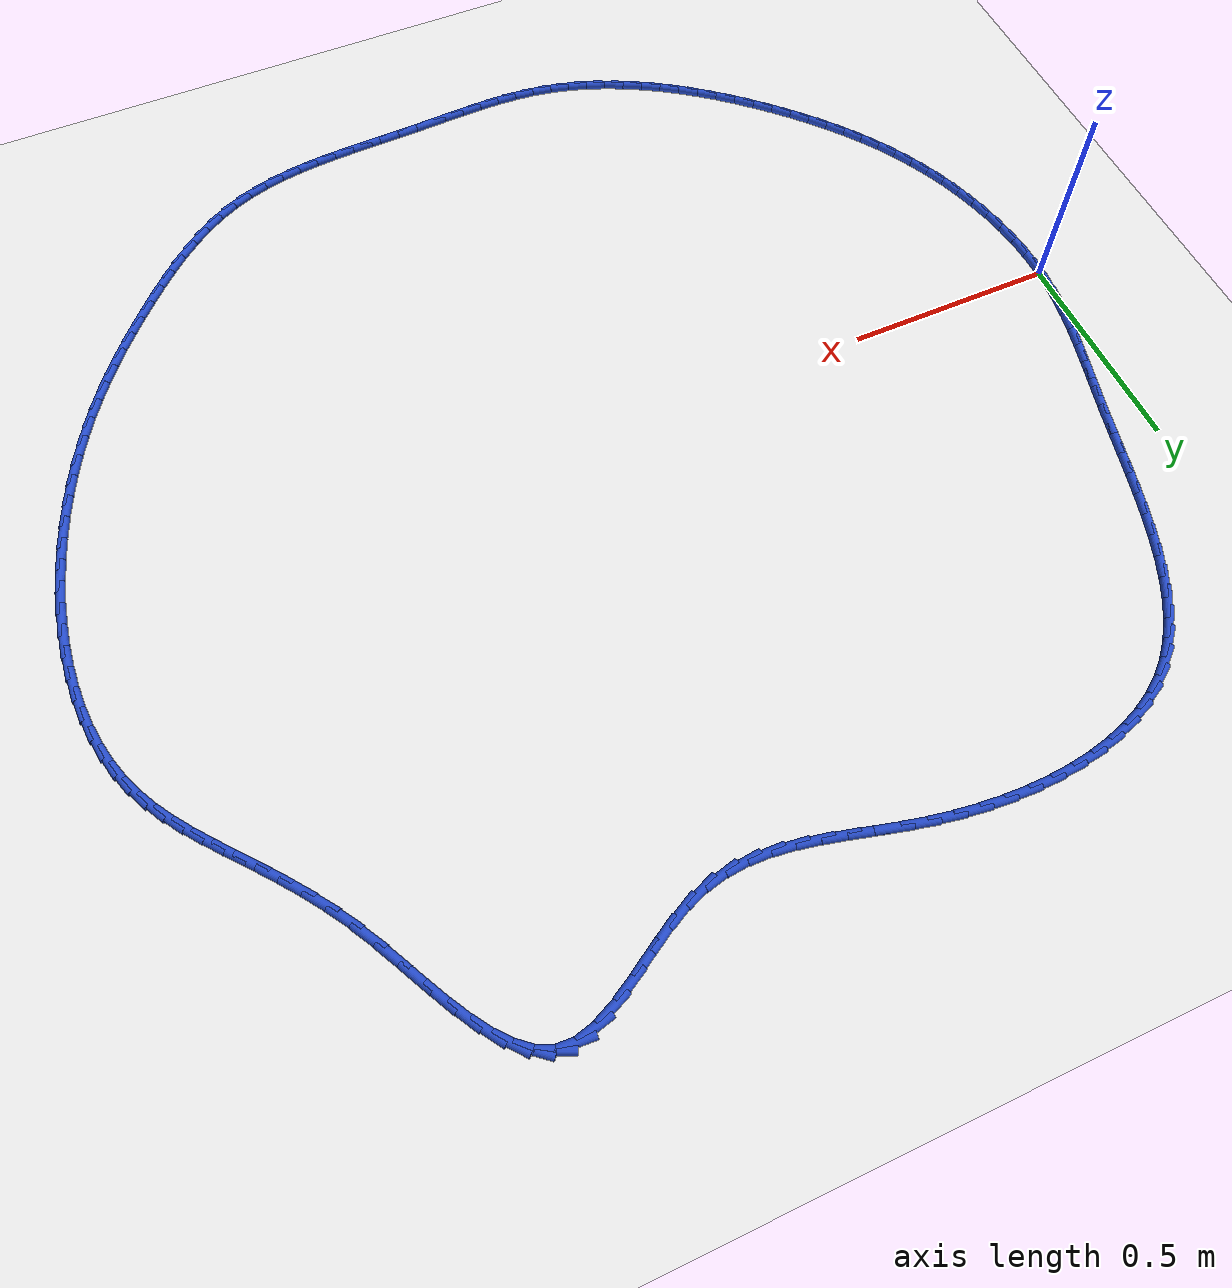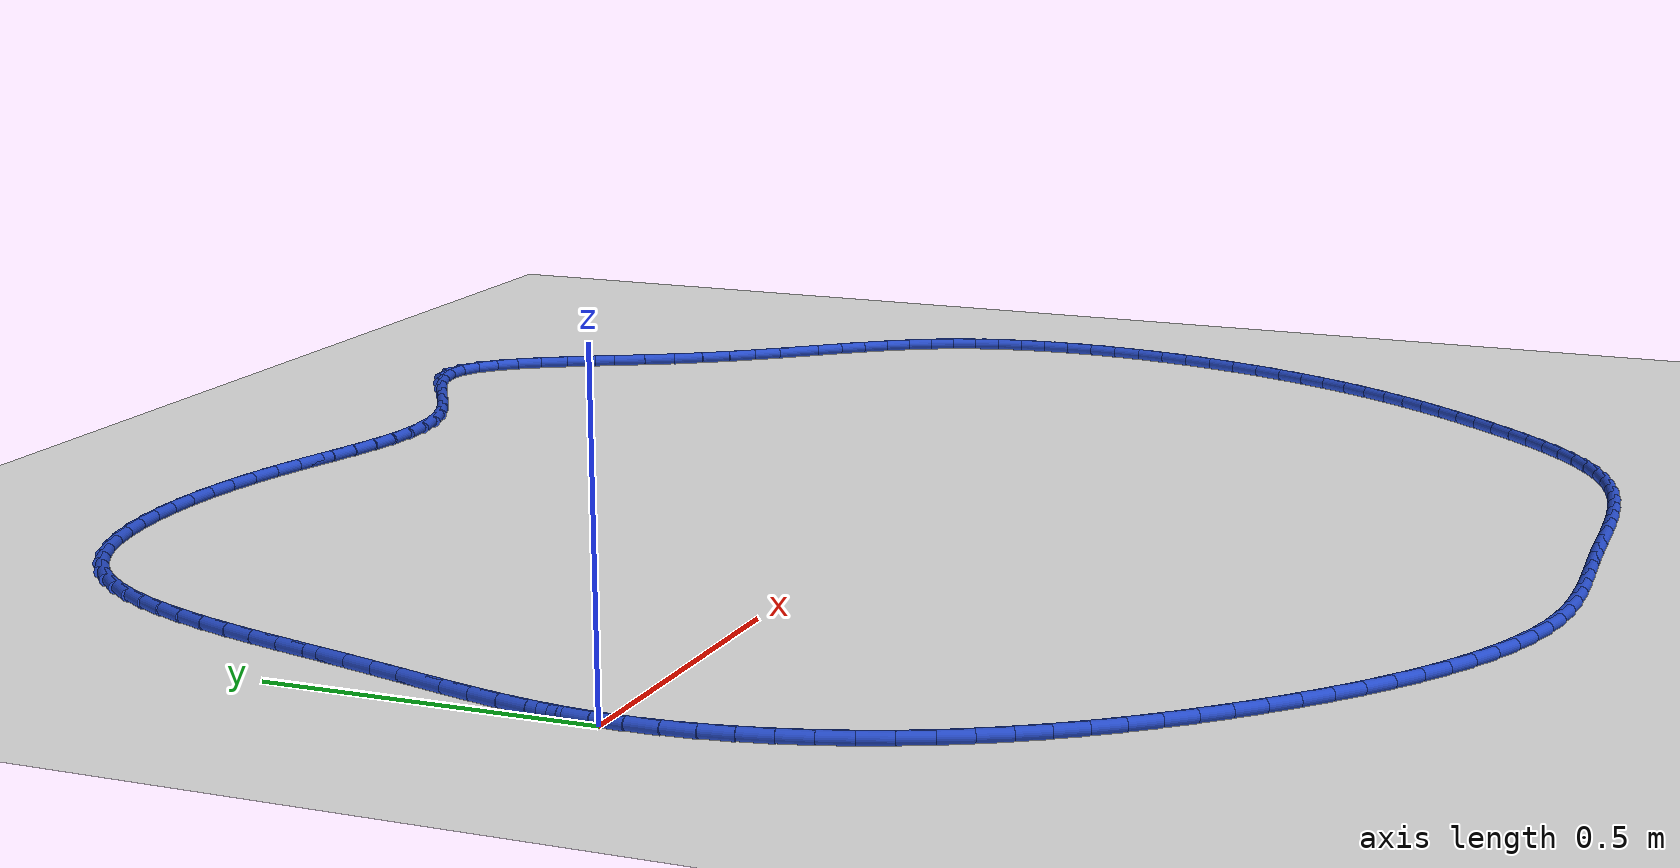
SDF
<sdf version="1.6">
 <world name="default">
  <light name="sun" type="directional">
   <pose>0 0 10 0 -0 0</pose>
   <diffuse>0.8 0.8 0.8 1</diffuse>
   <specular>0.2 0.2 0.2 1</specular>
   <attenuation>
    <range>1000</range>
    <constant>0.9</constant>
    <linear>0.01</linear>
    <quadratic>0.001</quadratic>
   </attenuation>
   <direction>-0.5 0.1 -0.9</direction>
  </light>
  <model name="ground_plane">
   <static>1</static>
   <link name="link">
    <collision name="collision">
     <geometry><plane><normal>0 0 1</normal><size>100 100</size></plane></geometry>
     <surface><friction><ode><mu>100</mu><mu2>50</mu2></ode></friction></surface>
    </collision>
    <visual name="visual">
     <cast_shadows>0</cast_shadows>
     <geometry><plane><normal>0 0 1</normal><size>100 100</size></plane></geometry>
     <material>
      <script><uri>file://media/materials/scripts/gazebo.material</uri><name>Gazebo/WhiteGlow</name></script>
     </material>
    </visual>
   </link>
  </model>
  <gravity>0 0 -9.8</gravity>
  <magnetic_field>6e-06 2.3e-05 -4.2e-05</magnetic_field>
  <atmosphere type="adiabatic"/>
  <physics name="default_physics" default="0" type="ode">
   <max_step_size>0.001</max_step_size>
   <real_time_factor>1</real_time_factor>
   <real_time_update_rate>1000</real_time_update_rate>
  </physics>
  <scene><ambient>0.4 0.4 0.4 1</ambient><background>0.7 0.7 0.7 1</background><shadows>1</shadows></scene>
  <spherical_coordinates>
   <surface_model>EARTH_WGS84</surface_model>
   <latitude_deg>0</latitude_deg>
   <longitude_deg>0</longitude_deg>
   <elevation>0</elevation>
   <heading_deg>0</heading_deg>
  </spherical_coordinates>
  <model name="line">
   <link name="link_0">
    <pose>4.163336342344337e-17 -4.163336342344337e-17 0.01 0 1.57 1.4999124152233703</pose>
    <collision name="collision">
     <geometry><cylinder><radius>0.01</radius><length>0.08</length></cylinder></geometry>
    </collision>
    <visual name="visual">
     <material>
      <script><name>Gazebo/Blue</name><uri>file://media/materials/scripts/gazebo.material</uri></script>
     </material>
     <geometry><cylinder><radius>0.01</radius><length>0.08</length></cylinder></geometry>
    </visual>
   </link>
   <link name="link_1">
    <pose>0.0034353470752524332 0.048383214245473635 0.01 0 1.57 1.4416949362031128</pose>
    <collision name="collision">
     <geometry><cylinder><radius>0.01</radius><length>0.08</length></cylinder></geometry>
    </collision>
    <visual name="visual">
     <material>
      <script><name>Gazebo/Blue</name><uri>file://media/materials/scripts/gazebo.material</uri></script>
     </material>
     <geometry><cylinder><radius>0.01</radius><length>0.08</length></cylinder></geometry>
    </visual>
   </link>
   <link name="link_2">
    <pose>0.009661087107435296 0.09633864696921361 0.01 0 1.57 1.3930272597436628</pose>
    <collision name="collision">
     <geometry><cylinder><radius>0.01</radius><length>0.08</length></cylinder></geometry>
    </collision>
    <visual name="visual">
     <material>
      <script><name>Gazebo/Blue</name><uri>file://media/materials/scripts/gazebo.material</uri></script>
     </material>
     <geometry><cylinder><radius>0.01</radius><length>0.08</length></cylinder></geometry>
    </visual>
   </link>
   <link name="link_3">
    <pose>0.018235313277014924 0.14406188141612447 0.01 0 1.57 1.354451068673993</pose>
    <collision name="collision">
     <geometry><cylinder><radius>0.01</radius><length>0.08</length></cylinder></geometry>
    </collision>
    <visual name="visual">
     <material>
      <script><name>Gazebo/Blue</name><uri>file://media/materials/scripts/gazebo.material</uri></script>
     </material>
     <geometry><cylinder><radius>0.01</radius><length>0.08</length></cylinder></geometry>
    </visual>
   </link>
   <link name="link_4">
    <pose>0.028716118764457628 0.1917485008311106 0.01 0 1.57 1.326130831242125</pose>
    <collision name="collision">
     <geometry><cylinder><radius>0.01</radius><length>0.08</length></cylinder></geometry>
    </collision>
    <visual name="visual">
     <material>
      <script><name>Gazebo/Blue</name><uri>file://media/materials/scripts/gazebo.material</uri></script>
     </material>
     <geometry><cylinder><radius>0.01</radius><length>0.08</length></cylinder></geometry>
    </visual>
   </link>
   <link name="link_5">
    <pose>0.040661596750229706 0.23959408845907665 0.01 0 1.57 1.3079702271599378</pose>
    <collision name="collision">
     <geometry><cylinder><radius>0.01</radius><length>0.08</length></cylinder></geometry>
    </collision>
    <visual name="visual">
     <material>
      <script><name>Gazebo/Blue</name><uri>file://media/materials/scripts/gazebo.material</uri></script>
     </material>
     <geometry><cylinder><radius>0.01</radius><length>0.08</length></cylinder></geometry>
    </visual>
   </link>
   <link name="link_6">
    <pose>0.0536298404147975 0.2877942275449271 0.01 0 1.57 1.299709326841991</pose>
    <collision name="collision">
     <geometry><cylinder><radius>0.01</radius><length>0.08</length></cylinder></geometry>
    </collision>
    <visual name="visual">
     <material>
      <script><name>Gazebo/Blue</name><uri>file://media/materials/scripts/gazebo.material</uri></script>
     </material>
     <geometry><cylinder><radius>0.01</radius><length>0.08</length></cylinder></geometry>
    </visual>
   </link>
   <link name="link_7">
    <pose>0.06717894293862728 0.33654450133356645 0.01 0 1.57 1.3009908277633147</pose>
    <collision name="collision">
     <geometry><cylinder><radius>0.01</radius><length>0.08</length></cylinder></geometry>
    </collision>
    <visual name="visual">
     <material>
      <script><name>Gazebo/Blue</name><uri>file://media/materials/scripts/gazebo.material</uri></script>
     </material>
     <geometry><cylinder><radius>0.01</radius><length>0.08</length></cylinder></geometry>
    </visual>
   </link>
   <link name="link_8">
    <pose>0.08086699750218537 0.3860404930698991 0.01 0 1.57 1.3108145258172932</pose>
    <collision name="collision">
     <geometry><cylinder><radius>0.01</radius><length>0.08</length></cylinder></geometry>
    </collision>
    <visual name="visual">
     <material>
      <script><name>Gazebo/Blue</name><uri>file://media/materials/scripts/gazebo.material</uri></script>
     </material>
     <geometry><cylinder><radius>0.01</radius><length>0.08</length></cylinder></geometry>
    </visual>
   </link>
   <link name="link_9">
    <pose>0.09427803473987154 0.4364575368132178 0.01 0 1.57 1.3197980189375305</pose>
    <collision name="collision">
     <geometry><cylinder><radius>0.01</radius><length>0.08</length></cylinder></geometry>
    </collision>
    <visual name="visual">
     <material>
      <script><name>Gazebo/Blue</name><uri>file://media/materials/scripts/gazebo.material</uri></script>
     </material>
     <geometry><cylinder><radius>0.01</radius><length>0.08</length></cylinder></geometry>
    </visual>
   </link>
   <link name="link_10">
    <pose>0.10740459338260107 0.4876520472604256 0.01 0 1.57 1.320964912147967</pose>
    <collision name="collision">
     <geometry><cylinder><radius>0.01</radius><length>0.08</length></cylinder></geometry>
    </collision>
    <visual name="visual">
     <material>
      <script><name>Gazebo/Blue</name><uri>file://media/materials/scripts/gazebo.material</uri></script>
     </material>
     <geometry><cylinder><radius>0.01</radius><length>0.08</length></cylinder></geometry>
    </visual>
   </link>
   <link name="link_11">
    <pose>0.12056445771267803 0.5392265222221929 0.01 0 1.57 1.314303633338765</pose>
    <collision name="collision">
     <geometry><cylinder><radius>0.01</radius><length>0.08</length></cylinder></geometry>
    </collision>
    <visual name="visual">
     <material>
      <script><name>Gazebo/Blue</name><uri>file://media/materials/scripts/gazebo.material</uri></script>
     </material>
     <geometry><cylinder><radius>0.01</radius><length>0.08</length></cylinder></geometry>
    </visual>
   </link>
   <link name="link_12">
    <pose>0.13408442528488776 0.5907764229115376 0.01 0 1.57 1.2997287223550906</pose>
    <collision name="collision">
     <geometry><cylinder><radius>0.01</radius><length>0.08</length></cylinder></geometry>
    </collision>
    <visual name="visual">
     <material>
      <script><name>Gazebo/Blue</name><uri>file://media/materials/scripts/gazebo.material</uri></script>
     </material>
     <geometry><cylinder><radius>0.01</radius><length>0.08</length></cylinder></geometry>
    </visual>
   </link>
   <link name="link_13">
    <pose>0.1482912936540155 0.6418972105414772 0.01 0 1.57 1.276888892110378</pose>
    <collision name="collision">
     <geometry><cylinder><radius>0.01</radius><length>0.08</length></cylinder></geometry>
    </collision>
    <visual name="visual">
     <material>
      <script><name>Gazebo/Blue</name><uri>file://media/materials/scripts/gazebo.material</uri></script>
     </material>
     <geometry><cylinder><radius>0.01</radius><length>0.08</length></cylinder></geometry>
    </visual>
   </link>
   <link name="link_14">
    <pose>0.16351186037484663 0.6921843463250296 0.01 0 1.57 1.245171557616993</pose>
    <collision name="collision">
     <geometry><cylinder><radius>0.01</radius><length>0.08</length></cylinder></geometry>
    </collision>
    <visual name="visual">
     <material>
      <script><name>Gazebo/Blue</name><uri>file://media/materials/scripts/gazebo.material</uri></script>
     </material>
     <geometry><cylinder><radius>0.01</radius><length>0.08</length></cylinder></geometry>
    </visual>
   </link>
   <link name="link_15">
    <pose>0.18007292300216646 0.7412332914752128 0.01 0 1.57 1.2037107704767265</pose>
    <collision name="collision">
     <geometry><cylinder><radius>0.01</radius><length>0.08</length></cylinder></geometry>
    </collision>
    <visual name="visual">
     <material>
      <script><name>Gazebo/Blue</name><uri>file://media/materials/scripts/gazebo.material</uri></script>
     </material>
     <geometry><cylinder><radius>0.01</radius><length>0.08</length></cylinder></geometry>
    </visual>
   </link>
   <link name="link_16">
    <pose>0.19830127909076034 0.7886395072050445 0.01 0 1.57 1.1514143401315635</pose>
    <collision name="collision">
     <geometry><cylinder><radius>0.01</radius><length>0.08</length></cylinder></geometry>
    </collision>
    <visual name="visual">
     <material>
      <script><name>Gazebo/Blue</name><uri>file://media/materials/scripts/gazebo.material</uri></script>
     </material>
     <geometry><cylinder><radius>0.01</radius><length>0.08</length></cylinder></geometry>
    </visual>
   </link>
   <link name="link_17">
    <pose>0.21852372619541363 0.8339984547275427 0.01 0 1.57 1.0870371923979392</pose>
    <collision name="collision">
     <geometry><cylinder><radius>0.01</radius><length>0.08</length></cylinder></geometry>
    </collision>
    <visual name="visual">
     <material>
      <script><name>Gazebo/Blue</name><uri>file://media/materials/scripts/gazebo.material</uri></script>
     </material>
     <geometry><cylinder><radius>0.01</radius><length>0.08</length></cylinder></geometry>
    </visual>
   </link>
   <link name="link_18">
    <pose>0.24106706187091162 0.8769055952557255 0.01 0 1.57 1.0093423806022614</pose>
    <collision name="collision">
     <geometry><cylinder><radius>0.01</radius><length>0.08</length></cylinder></geometry>
    </collision>
    <visual name="visual">
     <material>
      <script><name>Gazebo/Blue</name><uri>file://media/materials/scripts/gazebo.material</uri></script>
     </material>
     <geometry><cylinder><radius>0.01</radius><length>0.08</length></cylinder></geometry>
    </visual>
   </link>
   <link name="link_19">
    <pose>0.26625808367203946 0.9169563900026099 0.01 0 1.57 0.9174003090735459</pose>
    <collision name="collision">
     <geometry><cylinder><radius>0.01</radius><length>0.08</length></cylinder></geometry>
    </collision>
    <visual name="visual">
     <material>
      <script><name>Gazebo/Blue</name><uri>file://media/materials/scripts/gazebo.material</uri></script>
     </material>
     <geometry><cylinder><radius>0.01</radius><length>0.08</length></cylinder></geometry>
    </visual>
   </link>
   <link name="link_20">
    <pose>0.2944235891535828 0.9537463001812146 0.01 0 1.57 0.8110569901007801</pose>
    <collision name="collision">
     <geometry><cylinder><radius>0.01</radius><length>0.08</length></cylinder></geometry>
    </collision>
    <visual name="visual">
     <material>
      <script><name>Gazebo/Blue</name><uri>file://media/materials/scripts/gazebo.material</uri></script>
     </material>
     <geometry><cylinder><radius>0.01</radius><length>0.08</length></cylinder></geometry>
    </visual>
   </link>
   <link name="link_21">
    <pose>0.32589037587032677 0.9868707870045567 0.01 0 1.57 0.6916712373433794</pose>
    <collision name="collision">
     <geometry><cylinder><radius>0.01</radius><length>0.08</length></cylinder></geometry>
    </collision>
    <visual name="visual">
     <material>
      <script><name>Gazebo/Blue</name><uri>file://media/materials/scripts/gazebo.material</uri></script>
     </material>
     <geometry><cylinder><radius>0.01</radius><length>0.08</length></cylinder></geometry>
    </visual>
   </link>
   <link name="link_22">
    <pose>0.3609795362950252 1.015929862541689 0.01 0 1.57 0.569696512831975</pose>
    <collision name="collision">
     <geometry><cylinder><radius>0.01</radius><length>0.08</length></cylinder></geometry>
    </collision>
    <visual name="visual">
     <material>
      <script><name>Gazebo/Blue</name><uri>file://media/materials/scripts/gazebo.material</uri></script>
     </material>
     <geometry><cylinder><radius>0.01</radius><length>0.08</length></cylinder></geometry>
    </visual>
   </link>
   <link name="link_23">
    <pose>0.3997282710340755 1.0407499950293335 0.01 0 1.57 0.45823090206540995</pose>
    <collision name="collision">
     <geometry><cylinder><radius>0.01</radius><length>0.08</length></cylinder></geometry>
    </collision>
    <visual name="visual">
     <material>
      <script><name>Gazebo/Blue</name><uri>file://media/materials/scripts/gazebo.material</uri></script>
     </material>
     <geometry><cylinder><radius>0.01</radius><length>0.08</length></cylinder></geometry>
    </visual>
   </link>
   <link name="link_24">
    <pose>0.44176440433598235 1.0614842059173524 0.01 0 1.57 0.35841765030997236</pose>
    <collision name="collision">
     <geometry><cylinder><radius>0.01</radius><length>0.08</length></cylinder></geometry>
    </collision>
    <visual name="visual">
     <material>
      <script><name>Gazebo/Blue</name><uri>file://media/materials/scripts/gazebo.material</uri></script>
     </material>
     <geometry><cylinder><radius>0.01</radius><length>0.08</length></cylinder></geometry>
    </visual>
   </link>
   <link name="link_25">
    <pose>0.4866838995707897 1.0783109315874535 0.01 0 1.57 0.26960151113923364</pose>
    <collision name="collision">
     <geometry><cylinder><radius>0.01</radius><length>0.08</length></cylinder></geometry>
    </collision>
    <visual name="visual">
     <material>
      <script><name>Gazebo/Blue</name><uri>file://media/materials/scripts/gazebo.material</uri></script>
     </material>
     <geometry><cylinder><radius>0.01</radius><length>0.08</length></cylinder></geometry>
    </visual>
   </link>
   <link name="link_26">
    <pose>0.5340827201085409 1.0914086084213441 0.01 0 1.57 0.19062778412722106</pose>
    <collision name="collision">
     <geometry><cylinder><radius>0.01</radius><length>0.08</length></cylinder></geometry>
    </collision>
    <visual name="visual">
     <material>
      <script><name>Gazebo/Blue</name><uri>file://media/materials/scripts/gazebo.material</uri></script>
     </material>
     <geometry><cylinder><radius>0.01</radius><length>0.08</length></cylinder></geometry>
    </visual>
   </link>
   <link name="link_27">
    <pose>0.5835568293192793 1.1009556728007326 0.01 0 1.57 0.12015059850430183</pose>
    <collision name="collision">
     <geometry><cylinder><radius>0.01</radius><length>0.08</length></cylinder></geometry>
    </collision>
    <visual name="visual">
     <material>
      <script><name>Gazebo/Blue</name><uri>file://media/materials/scripts/gazebo.material</uri></script>
     </material>
     <geometry><cylinder><radius>0.01</radius><length>0.08</length></cylinder></geometry>
    </visual>
   </link>
   <link name="link_28">
    <pose>0.6347021905730483 1.1071305611073263 0.01 0 1.57 0.05681727929494344</pose>
    <collision name="collision">
     <geometry><cylinder><radius>0.01</radius><length>0.08</length></cylinder></geometry>
    </collision>
    <visual name="visual">
     <material>
      <script><name>Gazebo/Blue</name><uri>file://media/materials/scripts/gazebo.material</uri></script>
     </material>
     <geometry><cylinder><radius>0.01</radius><length>0.08</length></cylinder></geometry>
    </visual>
   </link>
   <link name="link_29">
    <pose>0.687114767239892 1.1101117097228335 0.01 0 1.57 -0.0006410925364399232</pose>
    <collision name="collision">
     <geometry><cylinder><radius>0.01</radius><length>0.08</length></cylinder></geometry>
    </collision>
    <visual name="visual">
     <material>
      <script><name>Gazebo/Blue</name><uri>file://media/materials/scripts/gazebo.material</uri></script>
     </material>
     <geometry><cylinder><radius>0.01</radius><length>0.08</length></cylinder></geometry>
    </visual>
   </link>
   <link name="link_30">
    <pose>0.7403905226898531 1.110077555028962 0.01 0 1.57 -0.05337861340335495</pose>
    <collision name="collision">
     <geometry><cylinder><radius>0.01</radius><length>0.08</length></cylinder></geometry>
    </collision>
    <visual name="visual">
     <material>
      <script><name>Gazebo/Blue</name><uri>file://media/materials/scripts/gazebo.material</uri></script>
     </material>
     <geometry><cylinder><radius>0.01</radius><length>0.08</length></cylinder></geometry>
    </visual>
   </link>
   <link name="link_31">
    <pose>0.7941254202929756 1.107206533407419 0.01 0 1.57 -0.10243720802708102</pose>
    <collision name="collision">
     <geometry><cylinder><radius>0.01</radius><length>0.08</length></cylinder></geometry>
    </collision>
    <visual name="visual">
     <material>
      <script><name>Gazebo/Blue</name><uri>file://media/materials/scripts/gazebo.material</uri></script>
     </material>
     <geometry><cylinder><radius>0.01</radius><length>0.08</length></cylinder></geometry>
    </visual>
   </link>
   <link name="link_32">
    <pose>0.8479154234193029 1.1016770812399133 0.01 0 1.57 -0.14876706757113042</pose>
    <collision name="collision">
     <geometry><cylinder><radius>0.01</radius><length>0.08</length></cylinder></geometry>
    </collision>
    <visual name="visual">
     <material>
      <script><name>Gazebo/Blue</name><uri>file://media/materials/scripts/gazebo.material</uri></script>
     </material>
     <geometry><cylinder><radius>0.01</radius><length>0.08</length></cylinder></geometry>
    </visual>
   </link>
   <link name="link_33">
    <pose>0.9013564954388782 1.0936676349081518 0.01 0 1.57 -0.19324897520283918</pose>
    <collision name="collision">
     <geometry><cylinder><radius>0.01</radius><length>0.08</length></cylinder></geometry>
    </collision>
    <visual name="visual">
     <material>
      <script><name>Gazebo/Blue</name><uri>file://media/materials/scripts/gazebo.material</uri></script>
     </material>
     <geometry><cylinder><radius>0.01</radius><length>0.08</length></cylinder></geometry>
    </visual>
   </link>
   <link name="link_34">
    <pose>0.9540448167677809 1.0833569993125154 0.01 0 1.57 -0.23209550543244556</pose>
    <collision name="collision">
     <geometry><cylinder><radius>0.01</radius><length>0.08</length></cylinder></geometry>
    </collision>
    <visual name="visual">
     <material>
      <script><name>Gazebo/Blue</name><uri>file://media/materials/scripts/gazebo.material</uri></script>
     </material>
     <geometry><cylinder><radius>0.01</radius><length>0.08</length></cylinder></geometry>
    </visual>
   </link>
   <link name="link_35">
    <pose>1.005707493467105 1.0711462757196426 0.01 0 1.57 -0.2529793466269696</pose>
    <collision name="collision">
     <geometry><cylinder><radius>0.01</radius><length>0.08</length></cylinder></geometry>
    </collision>
    <visual name="visual">
     <material>
      <script><name>Gazebo/Blue</name><uri>file://media/materials/scripts/gazebo.material</uri></script>
     </material>
     <geometry><cylinder><radius>0.01</radius><length>0.08</length></cylinder></geometry>
    </visual>
   </link>
   <link name="link_36">
    <pose>1.056424154929865 1.0580351086051556 0.01 0 1.57 -0.2531648066757704</pose>
    <collision name="collision">
     <geometry><cylinder><radius>0.01</radius><length>0.08</length></cylinder></geometry>
    </collision>
    <visual name="visual">
     <material>
      <script><name>Gazebo/Blue</name><uri>file://media/materials/scripts/gazebo.material</uri></script>
     </material>
     <geometry><cylinder><radius>0.01</radius><length>0.08</length></cylinder></geometry>
    </visual>
   </link>
   <link name="link_37">
    <pose>1.1063331609234646 1.045122859721722 0.01 0 1.57 -0.23163239137726563</pose>
    <collision name="collision">
     <geometry><cylinder><radius>0.01</radius><length>0.08</length></cylinder></geometry>
    </collision>
    <visual name="visual">
     <material>
      <script><name>Gazebo/Blue</name><uri>file://media/materials/scripts/gazebo.material</uri></script>
     </material>
     <geometry><cylinder><radius>0.01</radius><length>0.08</length></cylinder></geometry>
    </visual>
   </link>
   <link name="link_38">
    <pose>1.1555728712153104 1.0335088908220096 0.01 0 1.57 -0.18700213575170258</pose>
    <collision name="collision">
     <geometry><cylinder><radius>0.01</radius><length>0.08</length></cylinder></geometry>
    </collision>
    <visual name="visual">
     <material>
      <script><name>Gazebo/Blue</name><uri>file://media/materials/scripts/gazebo.material</uri></script>
     </material>
     <geometry><cylinder><radius>0.01</radius><length>0.08</length></cylinder></geometry>
    </visual>
   </link>
   <link name="link_39">
    <pose>1.2042816455728071 1.0242925636586857 0.01 0 1.57 -0.11782451779806392</pose>
    <collision name="collision">
     <geometry><cylinder><radius>0.01</radius><length>0.08</length></cylinder></geometry>
    </collision>
    <visual name="visual">
     <material>
      <script><name>Gazebo/Blue</name><uri>file://media/materials/scripts/gazebo.material</uri></script>
     </material>
     <geometry><cylinder><radius>0.01</radius><length>0.08</length></cylinder></geometry>
    </visual>
   </link>
   <link name="link_40">
    <pose>1.2525978437633607 1.018573239984418 0.01 0 1.57 -0.02336054635019127</pose>
    <collision name="collision">
     <geometry><cylinder><radius>0.01</radius><length>0.08</length></cylinder></geometry>
    </collision>
    <visual name="visual">
     <material>
      <script><name>Gazebo/Blue</name><uri>file://media/materials/scripts/gazebo.material</uri></script>
     </material>
     <geometry><cylinder><radius>0.01</radius><length>0.08</length></cylinder></geometry>
    </visual>
   </link>
   <link name="link_41">
    <pose>1.300659825554377 1.0174502815518742 0.01 0 1.57 0.09508545396640276</pose>
    <collision name="collision">
     <geometry><cylinder><radius>0.01</radius><length>0.08</length></cylinder></geometry>
    </collision>
    <visual name="visual">
     <material>
      <script><name>Gazebo/Blue</name><uri>file://media/materials/scripts/gazebo.material</uri></script>
     </material>
     <geometry><cylinder><radius>0.01</radius><length>0.08</length></cylinder></geometry>
    </visual>
   </link>
   <link name="link_42">
    <pose>1.3486059507132602 1.0220230501137217 0.01 0 1.57 0.2326924779171556</pose>
    <collision name="collision">
     <geometry><cylinder><radius>0.01</radius><length>0.08</length></cylinder></geometry>
    </collision>
    <visual name="visual">
     <material>
      <script><name>Gazebo/Blue</name><uri>file://media/materials/scripts/gazebo.material</uri></script>
     </material>
     <geometry><cylinder><radius>0.01</radius><length>0.08</length></cylinder></geometry>
    </visual>
   </link>
   <link name="link_43">
    <pose>1.3965745790074164 1.033390907422628 0.01 0 1.57 0.3765830726978775</pose>
    <collision name="collision">
     <geometry><cylinder><radius>0.01</radius><length>0.08</length></cylinder></geometry>
    </collision>
    <visual name="visual">
     <material>
      <script><name>Gazebo/Blue</name><uri>file://media/materials/scripts/gazebo.material</uri></script>
     </material>
     <geometry><cylinder><radius>0.01</radius><length>0.08</length></cylinder></geometry>
    </visual>
   </link>
   <link name="link_44">
    <pose>1.4446691625939485 1.0524102026499016 0.01 0 1.57 0.4815172181390112</pose>
    <collision name="collision">
     <geometry><cylinder><radius>0.01</radius><length>0.08</length></cylinder></geometry>
    </collision>
    <visual name="visual">
     <material>
      <script><name>Gazebo/Blue</name><uri>file://media/materials/scripts/gazebo.material</uri></script>
     </material>
     <geometry><cylinder><radius>0.01</radius><length>0.08</length></cylinder></geometry>
    </visual>
   </link>
   <link name="link_45">
    <pose>1.4926397126503907 1.0774767726585655 0.01 0 1.57 0.534894861974571</pose>
    <collision name="collision">
     <geometry><cylinder><radius>0.01</radius><length>0.08</length></cylinder></geometry>
    </collision>
    <visual name="visual">
     <material>
      <script><name>Gazebo/Blue</name><uri>file://media/materials/scripts/gazebo.material</uri></script>
     </material>
     <geometry><cylinder><radius>0.01</radius><length>0.08</length></cylinder></geometry>
    </visual>
   </link>
   <link name="link_46">
    <pose>1.5400308412010468 1.1055565489700203 0.01 0 1.57 0.5440439084154823</pose>
    <collision name="collision">
     <geometry><cylinder><radius>0.01</radius><length>0.08</length></cylinder></geometry>
    </collision>
    <visual name="visual">
     <material>
      <script><name>Gazebo/Blue</name><uri>file://media/materials/scripts/gazebo.material</uri></script>
     </material>
     <geometry><cylinder><radius>0.01</radius><length>0.08</length></cylinder></geometry>
    </visual>
   </link>
   <link name="link_47">
    <pose>1.586384623658411 1.1335978042462127 0.01 0 1.57 0.5076027853361925</pose>
    <collision name="collision">
     <geometry><cylinder><radius>0.01</radius><length>0.08</length></cylinder></geometry>
    </collision>
    <visual name="visual">
     <material>
      <script><name>Gazebo/Blue</name><uri>file://media/materials/scripts/gazebo.material</uri></script>
     </material>
     <geometry><cylinder><radius>0.01</radius><length>0.08</length></cylinder></geometry>
    </visual>
   </link>
   <link name="link_48">
    <pose>1.6312431354349761 1.1585488111490905 0.01 0 1.57 0.41315270728176634</pose>
    <collision name="collision">
     <geometry><cylinder><radius>0.01</radius><length>0.08</length></cylinder></geometry>
    </collision>
    <visual name="visual">
     <material>
      <script><name>Gazebo/Blue</name><uri>file://media/materials/scripts/gazebo.material</uri></script>
     </material>
     <geometry><cylinder><radius>0.01</radius><length>0.08</length></cylinder></geometry>
    </visual>
   </link>
   <link name="link_49">
    <pose>1.674148451943235 1.1773578423406001 0.01 0 1.57 0.23313202911358047</pose>
    <collision name="collision">
     <geometry><cylinder><radius>0.01</radius><length>0.08</length></cylinder></geometry>
    </collision>
    <visual name="visual">
     <material>
      <script><name>Gazebo/Blue</name><uri>file://media/materials/scripts/gazebo.material</uri></script>
     </material>
     <geometry><cylinder><radius>0.01</radius><length>0.08</length></cylinder></geometry>
    </visual>
   </link>
   <link name="link_50">
    <pose>1.7146426485956823 1.1869731704826887 0.01 0 1.57 -0.06676547502860465</pose>
    <collision name="collision">
     <geometry><cylinder><radius>0.01</radius><length>0.08</length></cylinder></geometry>
    </collision>
    <visual name="visual">
     <material>
      <script><name>Gazebo/Blue</name><uri>file://media/materials/scripts/gazebo.material</uri></script>
     </material>
     <geometry><cylinder><radius>0.01</radius><length>0.08</length></cylinder></geometry>
    </visual>
   </link>
   <link name="link_51">
    <pose>1.7522897452074089 1.1844559027336639 0.01 0 1.57 -0.41085451281752644</pose>
    <collision name="collision">
     <geometry><cylinder><radius>0.01</radius><length>0.08</length></cylinder></geometry>
    </collision>
    <visual name="visual">
     <material>
      <script><name>Gazebo/Blue</name><uri>file://media/materials/scripts/gazebo.material</uri></script>
     </material>
     <geometry><cylinder><radius>0.01</radius><length>0.08</length></cylinder></geometry>
    </visual>
   </link>
   <link name="link_52">
    <pose>1.7871231773394185 1.1692808045427932 0.01 0 1.57 -0.6754572141994422</pose>
    <collision name="collision">
     <geometry><cylinder><radius>0.01</radius><length>0.08</length></cylinder></geometry>
    </collision>
    <visual name="visual">
     <material>
      <script><name>Gazebo/Blue</name><uri>file://media/materials/scripts/gazebo.material</uri></script>
     </material>
     <geometry><cylinder><radius>0.01</radius><length>0.08</length></cylinder></geometry>
    </visual>
   </link>
   <link name="link_53">
    <pose>1.8196269815825128 1.1432395574853076 0.01 0 1.57 -0.8514501343276414</pose>
    <collision name="collision">
     <geometry><cylinder><radius>0.01</radius><length>0.08</length></cylinder></geometry>
    </collision>
    <visual name="visual">
     <material>
      <script><name>Gazebo/Blue</name><uri>file://media/materials/scripts/gazebo.material</uri></script>
     </material>
     <geometry><cylinder><radius>0.01</radius><length>0.08</length></cylinder></geometry>
    </visual>
   </link>
   <link name="link_54">
    <pose>1.850303374012861 1.1082173190497888 0.01 0 1.57 -0.9621681207622425</pose>
    <collision name="collision">
     <geometry><cylinder><radius>0.01</radius><length>0.08</length></cylinder></geometry>
    </collision>
    <visual name="visual">
     <material>
      <script><name>Gazebo/Blue</name><uri>file://media/materials/scripts/gazebo.material</uri></script>
     </material>
     <geometry><cylinder><radius>0.01</radius><length>0.08</length></cylinder></geometry>
    </visual>
   </link>
   <link name="link_55">
    <pose>1.8796545707066348 1.0660992467248203 0.01 0 1.57 -1.0283446093188084</pose>
    <collision name="collision">
     <geometry><cylinder><radius>0.01</radius><length>0.08</length></cylinder></geometry>
    </collision>
    <visual name="visual">
     <material>
      <script><name>Gazebo/Blue</name><uri>file://media/materials/scripts/gazebo.material</uri></script>
     </material>
     <geometry><cylinder><radius>0.01</radius><length>0.08</length></cylinder></geometry>
    </visual>
   </link>
   <link name="link_56">
    <pose>1.9081827877400053 1.0187704979989847 0.01 0 1.57 -1.0626998042609304</pose>
    <collision name="collision">
     <geometry><cylinder><radius>0.01</radius><length>0.08</length></cylinder></geometry>
    </collision>
    <visual name="visual">
     <material>
      <script><name>Gazebo/Blue</name><uri>file://media/materials/scripts/gazebo.material</uri></script>
     </material>
     <geometry><cylinder><radius>0.01</radius><length>0.08</length></cylinder></geometry>
    </visual>
   </link>
   <link name="link_57">
    <pose>1.936390241189143 0.968116230360864 0.01 0 1.57 -1.0718394611843682</pose>
    <collision name="collision">
     <geometry><cylinder><radius>0.01</radius><length>0.08</length></cylinder></geometry>
    </collision>
    <visual name="visual">
     <material>
      <script><name>Gazebo/Blue</name><uri>file://media/materials/scripts/gazebo.material</uri></script>
     </material>
     <geometry><cylinder><radius>0.01</radius><length>0.08</length></cylinder></geometry>
    </visual>
   </link>
   <link name="link_58">
    <pose>1.9647791471302196 0.9160216012990413 0.01 0 1.57 -1.058119476177989</pose>
    <collision name="collision">
     <geometry><cylinder><radius>0.01</radius><length>0.08</length></cylinder></geometry>
    </collision>
    <visual name="visual">
     <material>
      <script><name>Gazebo/Blue</name><uri>file://media/materials/scripts/gazebo.material</uri></script>
     </material>
     <geometry><cylinder><radius>0.01</radius><length>0.08</length></cylinder></geometry>
    </visual>
   </link>
   <link name="link_59">
    <pose>1.993851721639406 0.8643717683020999 0.01 0 1.57 -1.0206494215341262</pose>
    <collision name="collision">
     <geometry><cylinder><radius>0.01</radius><length>0.08</length></cylinder></geometry>
    </collision>
    <visual name="visual">
     <material>
      <script><name>Gazebo/Blue</name><uri>file://media/materials/scripts/gazebo.material</uri></script>
     </material>
     <geometry><cylinder><radius>0.01</radius><length>0.08</length></cylinder></geometry>
    </visual>
   </link>
   <link name="link_60">
    <pose>2.0241061232113076 0.8150418504887914 0.01 0 1.57 -0.9686179806672512</pose>
    <collision name="collision">
     <geometry><cylinder><radius>0.01</radius><length>0.08</length></cylinder></geometry>
    </collision>
    <visual name="visual">
     <material>
      <script><name>Gazebo/Blue</name><uri>file://media/materials/scripts/gazebo.material</uri></script>
     </material>
     <geometry><cylinder><radius>0.01</radius><length>0.08</length></cylinder></geometry>
    </visual>
   </link>
   <link name="link_61">
    <pose>2.0557030129762452 0.7690720057317476 0.01 0 1.57 -0.9235868822994103</pose>
    <collision name="collision">
     <geometry><cylinder><radius>0.01</radius><length>0.08</length></cylinder></geometry>
    </collision>
    <visual name="visual">
     <material>
      <script><name>Gazebo/Blue</name><uri>file://media/materials/scripts/gazebo.material</uri></script>
     </material>
     <geometry><cylinder><radius>0.01</radius><length>0.08</length></cylinder></geometry>
    </visual>
   </link>
   <link name="link_62">
    <pose>2.0882172079015975 0.7260530260000932 0.01 0 1.57 -0.8893350564374755</pose>
    <collision name="collision">
     <geometry><cylinder><radius>0.01</radius><length>0.08</length></cylinder></geometry>
    </collision>
    <visual name="visual">
     <material>
      <script><name>Gazebo/Blue</name><uri>file://media/materials/scripts/gazebo.material</uri></script>
     </material>
     <geometry><cylinder><radius>0.01</radius><length>0.08</length></cylinder></geometry>
    </visual>
   </link>
   <link name="link_63">
    <pose>2.121165011489231 0.6854309422033175 0.01 0 1.57 -0.8672696808095234</pose>
    <collision name="collision">
     <geometry><cylinder><radius>0.01</radius><length>0.08</length></cylinder></geometry>
    </collision>
    <visual name="visual">
     <material>
      <script><name>Gazebo/Blue</name><uri>file://media/materials/scripts/gazebo.material</uri></script>
     </material>
     <geometry><cylinder><radius>0.01</radius><length>0.08</length></cylinder></geometry>
    </visual>
   </link>
   <link name="link_64">
    <pose>2.154062727241013 0.6466517852509075 0.01 0 1.57 -0.8586521716212228</pose>
    <collision name="collision">
     <geometry><cylinder><radius>0.01</radius><length>0.08</length></cylinder></geometry>
    </collision>
    <visual name="visual">
     <material>
      <script><name>Gazebo/Blue</name><uri>file://media/materials/scripts/gazebo.material</uri></script>
     </material>
     <geometry><cylinder><radius>0.01</radius><length>0.08</length></cylinder></geometry>
    </visual>
   </link>
   <link name="link_65">
    <pose>2.18642665865881 0.6091615860523518 0.01 0 1.57 -0.8646536499138596</pose>
    <collision name="collision">
     <geometry><cylinder><radius>0.01</radius><length>0.08</length></cylinder></geometry>
    </collision>
    <visual name="visual">
     <material>
      <script><name>Gazebo/Blue</name><uri>file://media/materials/scripts/gazebo.material</uri></script>
     </material>
     <geometry><cylinder><radius>0.01</radius><length>0.08</length></cylinder></geometry>
    </visual>
   </link>
   <link name="link_66">
    <pose>2.217773109244491 0.5724063755171388 0.01 0 1.57 -0.8863631071750743</pose>
    <collision name="collision">
     <geometry><cylinder><radius>0.01</radius><length>0.08</length></cylinder></geometry>
    </collision>
    <visual name="visual">
     <material>
      <script><name>Gazebo/Blue</name><uri>file://media/materials/scripts/gazebo.material</uri></script>
     </material>
     <geometry><cylinder><radius>0.01</radius><length>0.08</length></cylinder></geometry>
    </visual>
   </link>
   <link name="link_67">
    <pose>2.2476183824999216 0.5358321845547559 0.01 0 1.57 -0.9247012103780249</pose>
    <collision name="collision">
     <geometry><cylinder><radius>0.01</radius><length>0.08</length></cylinder></geometry>
    </collision>
    <visual name="visual">
     <material>
      <script><name>Gazebo/Blue</name><uri>file://media/materials/scripts/gazebo.material</uri></script>
     </material>
     <geometry><cylinder><radius>0.01</radius><length>0.08</length></cylinder></geometry>
    </visual>
   </link>
   <link name="link_68">
    <pose>2.2754787819269695 0.4988850440746924 0.01 0 1.57 -0.9801942524848771</pose>
    <collision name="collision">
     <geometry><cylinder><radius>0.01</radius><length>0.08</length></cylinder></geometry>
    </collision>
    <visual name="visual">
     <material>
      <script><name>Gazebo/Blue</name><uri>file://media/materials/scripts/gazebo.material</uri></script>
     </material>
     <geometry><cylinder><radius>0.01</radius><length>0.08</length></cylinder></geometry>
    </visual>
   </link>
   <link name="link_69">
    <pose>2.3008706110275017 0.4610109849864359 0.01 0 1.57 -1.0525889060531999</pose>
    <collision name="collision">
     <geometry><cylinder><radius>0.01</radius><length>0.08</length></cylinder></geometry>
    </collision>
    <visual name="visual">
     <material>
      <script><name>Gazebo/Blue</name><uri>file://media/materials/scripts/gazebo.material</uri></script>
     </material>
     <geometry><cylinder><radius>0.01</radius><length>0.08</length></cylinder></geometry>
    </visual>
   </link>
   <link name="link_70">
    <pose>2.323310173303385 0.4216560381994746 0.01 0 1.57 -1.13982109331925</pose>
    <collision name="collision">
     <geometry><cylinder><radius>0.01</radius><length>0.08</length></cylinder></geometry>
    </collision>
    <visual name="visual">
     <material>
      <script><name>Gazebo/Blue</name><uri>file://media/materials/scripts/gazebo.material</uri></script>
     </material>
     <geometry><cylinder><radius>0.01</radius><length>0.08</length></cylinder></geometry>
    </visual>
   </link>
   <link name="link_71">
    <pose>2.3423310894931917 0.3802884061911581 0.01 0 1.57 -1.2295295904677952</pose>
    <collision name="collision">
     <geometry><cylinder><radius>0.01</radius><length>0.08</length></cylinder></geometry>
    </collision>
    <visual name="visual">
     <material>
      <script><name>Gazebo/Blue</name><uri>file://media/materials/scripts/gazebo.material</uri></script>
     </material>
     <geometry><cylinder><radius>0.01</radius><length>0.08</length></cylinder></geometry>
    </visual>
   </link>
   <link name="link_72">
    <pose>2.3577832313403824 0.3367811932563661 0.01 0 1.57 -1.3122969676908305</pose>
    <collision name="collision">
     <geometry><cylinder><radius>0.01</radius><length>0.08</length></cylinder></geometry>
    </collision>
    <visual name="visual">
     <material>
      <script><name>Gazebo/Blue</name><uri>file://media/materials/scripts/gazebo.material</uri></script>
     </material>
     <geometry><cylinder><radius>0.01</radius><length>0.08</length></cylinder></geometry>
    </visual>
   </link>
   <link name="link_73">
    <pose>2.3697929119557437 0.29136143651655894 0.01 0 1.57 -1.3880580985653634</pose>
    <collision name="collision">
     <geometry><cylinder><radius>0.01</radius><length>0.08</length></cylinder></geometry>
    </collision>
    <visual name="visual">
     <material>
      <script><name>Gazebo/Blue</name><uri>file://media/materials/scripts/gazebo.material</uri></script>
     </material>
     <geometry><cylinder><radius>0.01</radius><length>0.08</length></cylinder></geometry>
    </visual>
   </link>
   <link name="link_74">
    <pose>2.378495754555498 0.24426809298769364 0.01 0 1.57 -1.4572977745761642</pose>
    <collision name="collision">
     <geometry><cylinder><radius>0.01</radius><length>0.08</length></cylinder></geometry>
    </collision>
    <visual name="visual">
     <material>
      <script><name>Gazebo/Blue</name><uri>file://media/materials/scripts/gazebo.material</uri></script>
     </material>
     <geometry><cylinder><radius>0.01</radius><length>0.08</length></cylinder></geometry>
    </visual>
   </link>
   <link name="link_75">
    <pose>2.3840273823558675 0.1957401196857268 0.01 0 1.57 -1.52064025362172</pose>
    <collision name="collision">
     <geometry><cylinder><radius>0.01</radius><length>0.08</length></cylinder></geometry>
    </collision>
    <visual name="visual">
     <material>
      <script><name>Gazebo/Blue</name><uri>file://media/materials/scripts/gazebo.material</uri></script>
     </material>
     <geometry><cylinder><radius>0.01</radius><length>0.08</length></cylinder></geometry>
    </visual>
   </link>
   <link name="link_76">
    <pose>2.3865234185730744 0.1460164736266149 0.01 0 1.57 1.5628263048260254</pose>
    <collision name="collision">
     <geometry><cylinder><radius>0.01</radius><length>0.08</length></cylinder></geometry>
    </collision>
    <visual name="visual">
     <material>
      <script><name>Gazebo/Blue</name><uri>file://media/materials/scripts/gazebo.material</uri></script>
     </material>
     <geometry><cylinder><radius>0.01</radius><length>0.08</length></cylinder></geometry>
    </visual>
   </link>
   <link name="link_77">
    <pose>2.386119486423341 0.09533611182631498 0.01 0 1.57 1.5092323331376005</pose>
    <collision name="collision">
     <geometry><cylinder><radius>0.01</radius><length>0.08</length></cylinder></geometry>
    </collision>
    <visual name="visual">
     <material>
      <script><name>Gazebo/Blue</name><uri>file://media/materials/scripts/gazebo.material</uri></script>
     </material>
     <geometry><cylinder><radius>0.01</radius><length>0.08</length></cylinder></geometry>
    </visual>
   </link>
   <link name="link_78">
    <pose>2.38295120912289 0.04393799130078455 0.01 0 1.57 1.4595127516049173</pose>
    <collision name="collision">
     <geometry><cylinder><radius>0.01</radius><length>0.08</length></cylinder></geometry>
    </collision>
    <visual name="visual">
     <material>
      <script><name>Gazebo/Blue</name><uri>file://media/materials/scripts/gazebo.material</uri></script>
     </material>
     <geometry><cylinder><radius>0.01</radius><length>0.08</length></cylinder></geometry>
    </visual>
   </link>
   <link name="link_79">
    <pose>2.377154209887942 -0.007938930934021149 0.01 0 1.57 1.4130501560871613</pose>
    <collision name="collision">
     <geometry><cylinder><radius>0.01</radius><length>0.08</length></cylinder></geometry>
    </collision>
    <visual name="visual">
     <material>
      <script><name>Gazebo/Blue</name><uri>file://media/materials/scripts/gazebo.material</uri></script>
     </material>
     <geometry><cylinder><radius>0.01</radius><length>0.08</length></cylinder></geometry>
    </visual>
   </link>
   <link name="link_80">
    <pose>2.368864111934722 -0.060055697862143785 0.01 0 1.57 1.369270758628455</pose>
    <collision name="collision">
     <geometry><cylinder><radius>0.01</radius><length>0.08</length></cylinder></geometry>
    </collision>
    <visual name="visual">
     <material>
      <script><name>Gazebo/Blue</name><uri>file://media/materials/scripts/gazebo.material</uri></script>
     </material>
     <geometry><cylinder><radius>0.01</radius><length>0.08</length></cylinder></geometry>
    </visual>
   </link>
   <link name="link_81">
    <pose>2.35821653847945 -0.11217335246762836 0.01 0 1.57 1.3276411852856618</pose>
    <collision name="collision">
     <geometry><cylinder><radius>0.01</radius><length>0.08</length></cylinder></geometry>
    </collision>
    <visual name="visual">
     <material>
      <script><name>Gazebo/Blue</name><uri>file://media/materials/scripts/gazebo.material</uri></script>
     </material>
     <geometry><cylinder><radius>0.01</radius><length>0.08</length></cylinder></geometry>
    </visual>
   </link>
   <link name="link_82">
    <pose>2.3453471127383496 -0.16405293773451715 0.01 0 1.57 1.2876613845788</pose>
    <collision name="collision">
     <geometry><cylinder><radius>0.01</radius><length>0.08</length></cylinder></geometry>
    </collision>
    <visual name="visual">
     <material>
      <script><name>Gazebo/Blue</name><uri>file://media/materials/scripts/gazebo.material</uri></script>
     </material>
     <geometry><cylinder><radius>0.01</radius><length>0.08</length></cylinder></geometry>
    </visual>
   </link>
   <link name="link_83">
    <pose>2.330391457927643 -0.2154554966468527 0.01 0 1.57 1.2488551633261287</pose>
    <collision name="collision">
     <geometry><cylinder><radius>0.01</radius><length>0.08</length></cylinder></geometry>
    </collision>
    <visual name="visual">
     <material>
      <script><name>Gazebo/Blue</name><uri>file://media/materials/scripts/gazebo.material</uri></script>
     </material>
     <geometry><cylinder><radius>0.01</radius><length>0.08</length></cylinder></geometry>
    </visual>
   </link>
   <link name="link_84">
    <pose>2.3134851972635513 -0.2661420721886798 0.01 0 1.57 1.2107590940924304</pose>
    <collision name="collision">
     <geometry><cylinder><radius>0.01</radius><length>0.08</length></cylinder></geometry>
    </collision>
    <visual name="visual">
     <material>
      <script><name>Gazebo/Blue</name><uri>file://media/materials/scripts/gazebo.material</uri></script>
     </material>
     <geometry><cylinder><radius>0.01</radius><length>0.08</length></cylinder></geometry>
    </visual>
   </link>
   <link name="link_85">
    <pose>2.294763953962299 -0.3158737073440403 0.01 0 1.57 1.1729099934525988</pose>
    <collision name="collision">
     <geometry><cylinder><radius>0.01</radius><length>0.08</length></cylinder></geometry>
    </collision>
    <visual name="visual">
     <material>
      <script><name>Gazebo/Blue</name><uri>file://media/materials/scripts/gazebo.material</uri></script>
     </material>
     <geometry><cylinder><radius>0.01</radius><length>0.08</length></cylinder></geometry>
    </visual>
   </link>
   <link name="link_86">
    <pose>2.274363351240106 -0.36441144509697876 0.01 0 1.57 1.1348307691559723</pose>
    <collision name="collision">
     <geometry><cylinder><radius>0.01</radius><length>0.08</length></cylinder></geometry>
    </collision>
    <visual name="visual">
     <material>
      <script><name>Gazebo/Blue</name><uri>file://media/materials/scripts/gazebo.material</uri></script>
     </material>
     <geometry><cylinder><radius>0.01</radius><length>0.08</length></cylinder></geometry>
    </visual>
   </link>
   <link name="link_87">
    <pose>2.2524190123131955 -0.41151632843153774 0.01 0 1.57 1.096062313885386</pose>
    <collision name="collision">
     <geometry><cylinder><radius>0.01</radius><length>0.08</length></cylinder></geometry>
    </collision>
    <visual name="visual">
     <material>
      <script><name>Gazebo/Blue</name><uri>file://media/materials/scripts/gazebo.material</uri></script>
     </material>
     <geometry><cylinder><radius>0.01</radius><length>0.08</length></cylinder></geometry>
    </visual>
   </link>
   <link name="link_88">
    <pose>2.229064409681126 -0.45695897223915677 0.01 0 1.57 1.0573435636895376</pose>
    <collision name="collision">
     <geometry><cylinder><radius>0.01</radius><length>0.08</length></cylinder></geometry>
    </collision>
    <visual name="visual">
     <material>
      <script><name>Gazebo/Blue</name><uri>file://media/materials/scripts/gazebo.material</uri></script>
     </material>
     <geometry><cylinder><radius>0.01</radius><length>0.08</length></cylinder></geometry>
    </visual>
   </link>
   <link name="link_89">
    <pose>2.2043846949025516 -0.5007250469688461 0.01 0 1.57 1.0200967625125452</pose>
    <collision name="collision">
     <geometry><cylinder><radius>0.01</radius><length>0.08</length></cylinder></geometry>
    </collision>
    <visual name="visual">
     <material>
      <script><name>Gazebo/Blue</name><uri>file://media/materials/scripts/gazebo.material</uri></script>
     </material>
     <geometry><cylinder><radius>0.01</radius><length>0.08</length></cylinder></geometry>
    </visual>
   </link>
   <link name="link_90">
    <pose>2.1784173265674456 -0.5430124837951162 0.01 0 1.57 0.9848937162894433</pose>
    <collision name="collision">
     <geometry><cylinder><radius>0.01</radius><length>0.08</length></cylinder></geometry>
    </collision>
    <visual name="visual">
     <material>
      <script><name>Gazebo/Blue</name><uri>file://media/materials/scripts/gazebo.material</uri></script>
     </material>
     <geometry><cylinder><radius>0.01</radius><length>0.08</length></cylinder></geometry>
    </visual>
   </link>
   <link name="link_91">
    <pose>2.1511977381502954 -0.5840282268034769 0.01 0 1.57 0.9522070496805922</pose>
    <collision name="collision">
     <geometry><cylinder><radius>0.01</radius><length>0.08</length></cylinder></geometry>
    </collision>
    <visual name="visual">
     <material>
      <script><name>Gazebo/Blue</name><uri>file://media/materials/scripts/gazebo.material</uri></script>
     </material>
     <geometry><cylinder><radius>0.01</radius><length>0.08</length></cylinder></geometry>
    </visual>
   </link>
   <link name="link_92">
    <pose>2.1227613631255884 -0.6239792200794408 0.01 0 1.57 0.9224370843324163</pose>
    <collision name="collision">
     <geometry><cylinder><radius>0.01</radius><length>0.08</length></cylinder></geometry>
    </collision>
    <visual name="visual">
     <material>
      <script><name>Gazebo/Blue</name><uri>file://media/materials/scripts/gazebo.material</uri></script>
     </material>
     <geometry><cylinder><radius>0.01</radius><length>0.08</length></cylinder></geometry>
    </visual>
   </link>
   <link name="link_93">
    <pose>2.093143634967811 -0.663072407708517 0.01 0 1.57 0.8959001671479456</pose>
    <collision name="collision">
     <geometry><cylinder><radius>0.01</radius><length>0.08</length></cylinder></geometry>
    </collision>
    <visual name="visual">
     <material>
      <script><name>Gazebo/Blue</name><uri>file://media/materials/scripts/gazebo.material</uri></script>
     </material>
     <geometry><cylinder><radius>0.01</radius><length>0.08</length></cylinder></geometry>
    </visual>
   </link>
   <link name="link_94">
    <pose>2.0623799871514517 -0.7015147337762178 0.01 0 1.57 0.8728239710631356</pose>
    <collision name="collision">
     <geometry><cylinder><radius>0.01</radius><length>0.08</length></cylinder></geometry>
    </collision>
    <visual name="visual">
     <material>
      <script><name>Gazebo/Blue</name><uri>file://media/materials/scripts/gazebo.material</uri></script>
     </material>
     <geometry><cylinder><radius>0.01</radius><length>0.08</length></cylinder></geometry>
    </visual>
   </link>
   <link name="link_95">
    <pose>2.0305058531509967 -0.7395131423680534 0.01 0 1.57 0.8530415798553839</pose>
    <collision name="collision">
     <geometry><cylinder><radius>0.01</radius><length>0.08</length></cylinder></geometry>
    </collision>
    <visual name="visual">
     <material>
      <script><name>Gazebo/Blue</name><uri>file://media/materials/scripts/gazebo.material</uri></script>
     </material>
     <geometry><cylinder><radius>0.01</radius><length>0.08</length></cylinder></geometry>
    </visual>
   </link>
   <link name="link_96">
    <pose>1.9975533420515486 -0.7772549667868188 0.01 0 1.57 0.83038110487879</pose>
    <collision name="collision">
     <geometry><cylinder><radius>0.01</radius><length>0.08</length></cylinder></geometry>
    </collision>
    <visual name="visual">
     <material>
      <script><name>Gazebo/Blue</name><uri>file://media/materials/scripts/gazebo.material</uri></script>
     </material>
     <geometry><cylinder><radius>0.01</radius><length>0.08</length></cylinder></geometry>
    </visual>
   </link>
   <link name="link_97">
    <pose>1.963487537830247 -0.8145321549949883 0.01 0 1.57 0.7988435093050638</pose>
    <collision name="collision">
     <geometry><cylinder><radius>0.01</radius><length>0.08</length></cylinder></geometry>
    </collision>
    <visual name="visual">
     <material>
      <script><name>Gazebo/Blue</name><uri>file://media/materials/scripts/gazebo.material</uri></script>
     </material>
     <geometry><cylinder><radius>0.01</radius><length>0.08</length></cylinder></geometry>
    </visual>
   </link>
   <link name="link_98">
    <pose>1.928211356768369 -0.8507699237950992 0.01 0 1.57 0.757646637489345</pose>
    <collision name="collision">
     <geometry><cylinder><radius>0.01</radius><length>0.08</length></cylinder></geometry>
    </collision>
    <visual name="visual">
     <material>
      <script><name>Gazebo/Blue</name><uri>file://media/materials/scripts/gazebo.material</uri></script>
     </material>
     <geometry><cylinder><radius>0.01</radius><length>0.08</length></cylinder></geometry>
    </visual>
   </link>
   <link name="link_99">
    <pose>1.891625363964191 -0.8853796202128688 0.01 0 1.57 0.7059745853424321</pose>
    <collision name="collision">
     <geometry><cylinder><radius>0.01</radius><length>0.08</length></cylinder></geometry>
    </collision>
    <visual name="visual">
     <material>
      <script><name>Gazebo/Blue</name><uri>file://media/materials/scripts/gazebo.material</uri></script>
     </material>
     <geometry><cylinder><radius>0.01</radius><length>0.08</length></cylinder></geometry>
    </visual>
   </link>
   <link name="link_100">
    <pose>1.8536301245159947 -0.9177725912740133 0.01 0 1.57 0.6428471131550851</pose>
    <collision name="collision">
     <geometry><cylinder><radius>0.01</radius><length>0.08</length></cylinder></geometry>
    </collision>
    <visual name="visual">
     <material>
      <script><name>Gazebo/Blue</name><uri>file://media/materials/scripts/gazebo.material</uri></script>
     </material>
     <geometry><cylinder><radius>0.01</radius><length>0.08</length></cylinder></geometry>
    </visual>
   </link>
   <link name="link_101">
    <pose>1.8141262035220587 -0.9473601840042484 0.01 0 1.57 0.5672718865307994</pose>
    <collision name="collision">
     <geometry><cylinder><radius>0.01</radius><length>0.08</length></cylinder></geometry>
    </collision>
    <visual name="visual">
     <material>
      <script><name>Gazebo/Blue</name><uri>file://media/materials/scripts/gazebo.material</uri></script>
     </material>
     <geometry><cylinder><radius>0.01</radius><length>0.08</length></cylinder></geometry>
    </visual>
   </link>
   <link name="link_102">
    <pose>1.7730141660806615 -0.9735537454292917 0.01 0 1.57 0.478535032240379</pose>
    <collision name="collision">
     <geometry><cylinder><radius>0.01</radius><length>0.08</length></cylinder></geometry>
    </collision>
    <visual name="visual">
     <material>
      <script><name>Gazebo/Blue</name><uri>file://media/materials/scripts/gazebo.material</uri></script>
     </material>
     <geometry><cylinder><radius>0.01</radius><length>0.08</length></cylinder></geometry>
    </visual>
   </link>
   <link name="link_103">
    <pose>1.7301950101969013 -0.9957661926345591 0.01 0 1.57 0.38328983788159293</pose>
    <collision name="collision">
     <geometry><cylinder><radius>0.01</radius><length>0.08</length></cylinder></geometry>
    </collision>
    <visual name="visual">
     <material>
      <script><name>Gazebo/Blue</name><uri>file://media/materials/scripts/gazebo.material</uri></script>
     </material>
     <geometry><cylinder><radius>0.01</radius><length>0.08</length></cylinder></geometry>
    </visual>
   </link>
   <link name="link_104">
    <pose>1.6856566089899627 -1.0137255200149022 0.01 0 1.57 0.2975214215037489</pose>
    <collision name="collision">
     <geometry><cylinder><radius>0.01</radius><length>0.08</length></cylinder></geometry>
    </collision>
    <visual name="visual">
     <material>
      <script><name>Gazebo/Blue</name><uri>file://media/materials/scripts/gazebo.material</uri></script>
     </material>
     <geometry><cylinder><radius>0.01</radius><length>0.08</length></cylinder></geometry>
    </visual>
   </link>
   <link name="link_105">
    <pose>1.6395783120928236 -1.0278541660004004 0.01 0 1.57 0.22422469611445223</pose>
    <collision name="collision">
     <geometry><cylinder><radius>0.01</radius><length>0.08</length></cylinder></geometry>
    </collision>
    <visual name="visual">
     <material>
      <script><name>Gazebo/Blue</name><uri>file://media/materials/scripts/gazebo.material</uri></script>
     </material>
     <geometry><cylinder><radius>0.01</radius><length>0.08</length></cylinder></geometry>
    </visual>
   </link>
   <link name="link_106">
    <pose>1.592165016321856 -1.0386672231475893 0.01 0 1.57 0.16358477978292887</pose>
    <collision name="collision">
     <geometry><cylinder><radius>0.01</radius><length>0.08</length></cylinder></geometry>
    </collision>
    <visual name="visual">
     <material>
      <script><name>Gazebo/Blue</name><uri>file://media/materials/scripts/gazebo.material</uri></script>
     </material>
     <geometry><cylinder><radius>0.01</radius><length>0.08</length></cylinder></geometry>
    </visual>
   </link>
   <link name="link_107">
    <pose>1.5436216184934282 -1.0466797840130073 0.01 0 1.57 0.11526043984054417</pose>
    <collision name="collision">
     <geometry><cylinder><radius>0.01</radius><length>0.08</length></cylinder></geometry>
    </collision>
    <visual name="visual">
     <material>
      <script><name>Gazebo/Blue</name><uri>file://media/materials/scripts/gazebo.material</uri></script>
     </material>
     <geometry><cylinder><radius>0.01</radius><length>0.08</length></cylinder></geometry>
    </visual>
   </link>
   <link name="link_108">
    <pose>1.4941530154239118 -1.0524069411531896 0.01 0 1.57 0.0786763099876842</pose>
    <collision name="collision">
     <geometry><cylinder><radius>0.01</radius><length>0.08</length></cylinder></geometry>
    </collision>
    <visual name="visual">
     <material>
      <script><name>Gazebo/Blue</name><uri>file://media/materials/scripts/gazebo.material</uri></script>
     </material>
     <geometry><cylinder><radius>0.01</radius><length>0.08</length></cylinder></geometry>
    </visual>
   </link>
   <link name="link_109">
    <pose>1.443964103929679 -1.0563637871246736 0.01 0 1.57 0.05323165613091327</pose>
    <collision name="collision">
     <geometry><cylinder><radius>0.01</radius><length>0.08</length></cylinder></geometry>
    </collision>
    <visual name="visual">
     <material>
      <script><name>Gazebo/Blue</name><uri>file://media/materials/scripts/gazebo.material</uri></script>
     </material>
     <geometry><cylinder><radius>0.01</radius><length>0.08</length></cylinder></geometry>
    </visual>
   </link>
   <link name="link_110">
    <pose>1.3932597808270972 -1.059065414483995 0.01 0 1.57 0.03843069253126035</pose>
    <collision name="collision">
     <geometry><cylinder><radius>0.01</radius><length>0.08</length></cylinder></geometry>
    </collision>
    <visual name="visual">
     <material>
      <script><name>Gazebo/Blue</name><uri>file://media/materials/scripts/gazebo.material</uri></script>
     </material>
     <geometry><cylinder><radius>0.01</radius><length>0.08</length></cylinder></geometry>
    </visual>
   </link>
   <link name="link_111">
    <pose>1.3422449429325385 -1.061026915787691 0.01 0 1.57 0.03395510409220163</pose>
    <collision name="collision">
     <geometry><cylinder><radius>0.01</radius><length>0.08</length></cylinder></geometry>
    </collision>
    <visual name="visual">
     <material>
      <script><name>Gazebo/Blue</name><uri>file://media/materials/scripts/gazebo.material</uri></script>
     </material>
     <geometry><cylinder><radius>0.01</radius><length>0.08</length></cylinder></geometry>
    </visual>
   </link>
   <link name="link_112">
    <pose>1.2911244870623737 -1.0627633835922978 0.01 0 1.57 0.039698460282382386</pose>
    <collision name="collision">
     <geometry><cylinder><radius>0.01</radius><length>0.08</length></cylinder></geometry>
    </collision>
    <visual name="visual">
     <material>
      <script><name>Gazebo/Blue</name><uri>file://media/materials/scripts/gazebo.material</uri></script>
     </material>
     <geometry><cylinder><radius>0.01</radius><length>0.08</length></cylinder></geometry>
    </visual>
   </link>
   <link name="link_113">
    <pose>1.240103310032972 -1.064789910454352 0.01 0 1.57 0.05246544620024934</pose>
    <collision name="collision">
     <geometry><cylinder><radius>0.01</radius><length>0.08</length></cylinder></geometry>
    </collision>
    <visual name="visual">
     <material>
      <script><name>Gazebo/Blue</name><uri>file://media/materials/scripts/gazebo.material</uri></script>
     </material>
     <geometry><cylinder><radius>0.01</radius><length>0.08</length></cylinder></geometry>
    </visual>
   </link>
   <link name="link_114">
    <pose>1.189360812319214 -1.0674545836339386 0.01 0 1.57 0.057577758863087504</pose>
    <collision name="collision">
     <geometry><cylinder><radius>0.01</radius><length>0.08</length></cylinder></geometry>
    </collision>
    <visual name="visual">
     <material>
      <script><name>Gazebo/Blue</name><uri>file://media/materials/scripts/gazebo.material</uri></script>
     </material>
     <geometry><cylinder><radius>0.01</radius><length>0.08</length></cylinder></geometry>
    </visual>
   </link>
   <link name="link_115">
    <pose>1.1389625232152158 -1.0703596151326569 0.01 0 1.57 0.050724875215369926</pose>
    <collision name="collision">
     <geometry><cylinder><radius>0.01</radius><length>0.08</length></cylinder></geometry>
    </collision>
    <visual name="visual">
     <material>
      <script><name>Gazebo/Blue</name><uri>file://media/materials/scripts/gazebo.material</uri></script>
     </material>
     <geometry><cylinder><radius>0.01</radius><length>0.08</length></cylinder></geometry>
    </visual>
   </link>
   <link name="link_116">
    <pose>1.0889421944295494 -1.072899068457681 0.01 0 1.57 0.03159547054111554</pose>
    <collision name="collision">
     <geometry><cylinder><radius>0.01</radius><length>0.08</length></cylinder></geometry>
    </collision>
    <visual name="visual">
     <material>
      <script><name>Gazebo/Blue</name><uri>file://media/materials/scripts/gazebo.material</uri></script>
     </material>
     <geometry><cylinder><radius>0.01</radius><length>0.08</length></cylinder></geometry>
    </visual>
   </link>
   <link name="link_117">
    <pose>1.0393335762587848 -1.0744669978673351 0.01 0 1.57 -0.00019405277856556258</pose>
    <collision name="collision">
     <geometry><cylinder><radius>0.01</radius><length>0.08</length></cylinder></geometry>
    </collision>
    <visual name="visual">
     <material>
      <script><name>Gazebo/Blue</name><uri>file://media/materials/scripts/gazebo.material</uri></script>
     </material>
     <geometry><cylinder><radius>0.01</radius><length>0.08</length></cylinder></geometry>
    </visual>
   </link>
   <link name="link_118">
    <pose>0.9901704189994891 -1.0744574576199462 0.01 0 1.57 -0.045014310405319946</pose>
    <collision name="collision">
     <geometry><cylinder><radius>0.01</radius><length>0.08</length></cylinder></geometry>
    </collision>
    <visual name="visual">
     <material>
      <script><name>Gazebo/Blue</name><uri>file://media/materials/scripts/gazebo.material</uri></script>
     </material>
     <geometry><cylinder><radius>0.01</radius><length>0.08</length></cylinder></geometry>
    </visual>
   </link>
   <link name="link_119">
    <pose>0.9414864729482333 -1.0722645019738397 0.01 0 1.57 -0.10306335883712651</pose>
    <collision name="collision">
     <geometry><cylinder><radius>0.01</radius><length>0.08</length></cylinder></geometry>
    </collision>
    <visual name="visual">
     <material>
      <script><name>Gazebo/Blue</name><uri>file://media/materials/scripts/gazebo.material</uri></script>
     </material>
     <geometry><cylinder><radius>0.01</radius><length>0.08</length></cylinder></geometry>
    </visual>
   </link>
   <link name="link_120">
    <pose>0.893315488401585 -1.0672821851873409 0.01 0 1.57 -0.17366013079080686</pose>
    <collision name="collision">
     <geometry><cylinder><radius>0.01</radius><length>0.08</length></cylinder></geometry>
    </collision>
    <visual name="visual">
     <material>
      <script><name>Gazebo/Blue</name><uri>file://media/materials/scripts/gazebo.material</uri></script>
     </material>
     <geometry><cylinder><radius>0.01</radius><length>0.08</length></cylinder></geometry>
    </visual>
   </link>
   <link name="link_121">
    <pose>0.8456918859040983 -1.0589277105036434 0.01 0 1.57 -0.24747377938195067</pose>
    <collision name="collision">
     <geometry><cylinder><radius>0.01</radius><length>0.08</length></cylinder></geometry>
    </collision>
    <visual name="visual">
     <material>
      <script><name>Gazebo/Blue</name><uri>file://media/materials/scripts/gazebo.material</uri></script>
     </material>
     <geometry><cylinder><radius>0.01</radius><length>0.08</length></cylinder></geometry>
    </visual>
   </link>
   <link name="link_122">
    <pose>0.7986624583795688 -1.047045597661309 0.01 0 1.57 -0.3165029469095039</pose>
    <collision name="collision">
     <geometry><cylinder><radius>0.01</radius><length>0.08</length></cylinder></geometry>
    </collision>
    <visual name="visual">
     <material>
      <script><name>Gazebo/Blue</name><uri>file://media/materials/scripts/gazebo.material</uri></script>
     </material>
     <geometry><cylinder><radius>0.01</radius><length>0.08</length></cylinder></geometry>
    </visual>
   </link>
   <link name="link_123">
    <pose>0.7522848848361743 -1.0318563493312705 0.01 0 1.57 -0.3804305643928669</pose>
    <collision name="collision">
     <geometry><cylinder><radius>0.01</radius><length>0.08</length></cylinder></geometry>
    </collision>
    <visual name="visual">
     <material>
      <script><name>Gazebo/Blue</name><uri>file://media/materials/scripts/gazebo.material</uri></script>
     </material>
     <geometry><cylinder><radius>0.01</radius><length>0.08</length></cylinder></geometry>
    </visual>
   </link>
   <link name="link_124">
    <pose>0.7066172157439903 -1.0135932977132354 0.01 0 1.57 -0.43937287315726503</pose>
    <collision name="collision">
     <geometry><cylinder><radius>0.01</radius><length>0.08</length></cylinder></geometry>
    </collision>
    <visual name="visual">
     <material>
      <script><name>Gazebo/Blue</name><uri>file://media/materials/scripts/gazebo.material</uri></script>
     </material>
     <geometry><cylinder><radius>0.01</radius><length>0.08</length></cylinder></geometry>
    </visual>
   </link>
   <link name="link_125">
    <pose>0.6617175015730925 -0.9924897750069123 0.01 0 1.57 -0.49356601585230947</pose>
    <collision name="collision">
     <geometry><cylinder><radius>0.01</radius><length>0.08</length></cylinder></geometry>
    </collision>
    <visual name="visual">
     <material>
      <script><name>Gazebo/Blue</name><uri>file://media/materials/scripts/gazebo.material</uri></script>
     </material>
     <geometry><cylinder><radius>0.01</radius><length>0.08</length></cylinder></geometry>
    </visual>
   </link>
   <link name="link_126">
    <pose>0.6176437927935544 -0.9687791134120084 0.01 0 1.57 -0.5433201645420623</pose>
    <collision name="collision">
     <geometry><cylinder><radius>0.01</radius><length>0.08</length></cylinder></geometry>
    </collision>
    <visual name="visual">
     <material>
      <script><name>Gazebo/Blue</name><uri>file://media/materials/scripts/gazebo.material</uri></script>
     </material>
     <geometry><cylinder><radius>0.01</radius><length>0.08</length></cylinder></geometry>
    </visual>
   </link>
   <link name="link_127">
    <pose>0.574454139875452 -0.9426946451282324 0.01 0 1.57 -0.5889837303029628</pose>
    <collision name="collision">
     <geometry><cylinder><radius>0.01</radius><length>0.08</length></cylinder></geometry>
    </collision>
    <visual name="visual">
     <material>
      <script><name>Gazebo/Blue</name><uri>file://media/materials/scripts/gazebo.material</uri></script>
     </material>
     <geometry><cylinder><radius>0.01</radius><length>0.08</length></cylinder></geometry>
    </visual>
   </link>
   <link name="link_128">
    <pose>0.5322065932888591 -0.9144697023552913 0.01 0 1.57 -0.6309175615037008</pose>
    <collision name="collision">
     <geometry><cylinder><radius>0.01</radius><length>0.08</length></cylinder></geometry>
    </collision>
    <visual name="visual">
     <material>
      <script><name>Gazebo/Blue</name><uri>file://media/materials/scripts/gazebo.material</uri></script>
     </material>
     <geometry><cylinder><radius>0.01</radius><length>0.08</length></cylinder></geometry>
    </visual>
   </link>
   <link name="link_129">
    <pose>0.49095920350385136 -0.8843376172928936 0.01 0 1.57 -0.6694776914363968</pose>
    <collision name="collision">
     <geometry><cylinder><radius>0.01</radius><length>0.08</length></cylinder></geometry>
    </collision>
    <visual name="visual">
     <material>
      <script><name>Gazebo/Blue</name><uri>file://media/materials/scripts/gazebo.material</uri></script>
     </material>
     <geometry><cylinder><radius>0.01</radius><length>0.08</length></cylinder></geometry>
    </visual>
   </link>
   <link name="link_130">
    <pose>0.4507700209905042 -0.8525317221407481 0.01 0 1.57 -0.7050047695344712</pose>
    <collision name="collision">
     <geometry><cylinder><radius>0.01</radius><length>0.08</length></cylinder></geometry>
    </collision>
    <visual name="visual">
     <material>
      <script><name>Gazebo/Blue</name><uri>file://media/materials/scripts/gazebo.material</uri></script>
     </material>
     <geometry><cylinder><radius>0.01</radius><length>0.08</length></cylinder></geometry>
    </visual>
   </link>
   <link name="link_131">
    <pose>0.41169709621889117 -0.819285349098561 0.01 0 1.57 -0.7378183965967664</pose>
    <collision name="collision">
     <geometry><cylinder><radius>0.01</radius><length>0.08</length></cylinder></geometry>
    </collision>
    <visual name="visual">
     <material>
      <script><name>Gazebo/Blue</name><uri>file://media/materials/scripts/gazebo.material</uri></script>
     </material>
     <geometry><cylinder><radius>0.01</radius><length>0.08</length></cylinder></geometry>
    </visual>
   </link>
   <link name="link_132">
    <pose>0.37379847965908874 -0.7848318303660421 0.01 0 1.57 -0.7682148921303728</pose>
    <collision name="collision">
     <geometry><cylinder><radius>0.01</radius><length>0.08</length></cylinder></geometry>
    </collision>
    <visual name="visual">
     <material>
      <script><name>Gazebo/Blue</name><uri>file://media/materials/scripts/gazebo.material</uri></script>
     </material>
     <geometry><cylinder><radius>0.01</radius><length>0.08</length></cylinder></geometry>
    </visual>
   </link>
   <link name="link_133">
    <pose>0.33713222178117025 -0.7494044981428978 0.01 0 1.57 -0.7969556815643154</pose>
    <collision name="collision">
     <geometry><cylinder><radius>0.01</radius><length>0.08</length></cylinder></geometry>
    </collision>
    <visual name="visual">
     <material>
      <script><name>Gazebo/Blue</name><uri>file://media/materials/scripts/gazebo.material</uri></script>
     </material>
     <geometry><cylinder><radius>0.01</radius><length>0.08</length></cylinder></geometry>
    </visual>
   </link>
   <link name="link_134">
    <pose>0.30176111922284904 -0.713206194035025 0.01 0 1.57 -0.8275589758012224</pose>
    <collision name="collision">
     <geometry><cylinder><radius>0.01</radius><length>0.08</length></cylinder></geometry>
    </collision>
    <visual name="visual">
     <material>
      <script><name>Gazebo/Blue</name><uri>file://media/materials/scripts/gazebo.material</uri></script>
     </material>
     <geometry><cylinder><radius>0.01</radius><length>0.08</length></cylinder></geometry>
    </visual>
   </link>
   <link name="link_135">
    <pose>0.26778029614630033 -0.6762320793697216 0.01 0 1.57 -0.8614622505158083</pose>
    <collision name="collision">
     <geometry><cylinder><radius>0.01</radius><length>0.08</length></cylinder></geometry>
    </collision>
    <visual name="visual">
     <material>
      <script><name>Gazebo/Blue</name><uri>file://media/materials/scripts/gazebo.material</uri></script>
     </material>
     <geometry><cylinder><radius>0.01</radius><length>0.08</length></cylinder></geometry>
    </visual>
   </link>
   <link name="link_136">
    <pose>0.23529835591907122 -0.6383907216142847 0.01 0 1.57 -0.8986671510943025</pose>
    <collision name="collision">
     <geometry><cylinder><radius>0.01</radius><length>0.08</length></cylinder></geometry>
    </collision>
    <visual name="visual">
     <material>
      <script><name>Gazebo/Blue</name><uri>file://media/materials/scripts/gazebo.material</uri></script>
     </material>
     <geometry><cylinder><radius>0.01</radius><length>0.08</length></cylinder></geometry>
    </visual>
   </link>
   <link name="link_137">
    <pose>0.20442394661371655 -0.5995904010396312 0.01 0 1.57 -0.9391226940878901</pose>
    <collision name="collision">
     <geometry><cylinder><radius>0.01</radius><length>0.08</length></cylinder></geometry>
    </collision>
    <visual name="visual">
     <material>
      <script><name>Gazebo/Blue</name><uri>file://media/materials/scripts/gazebo.material</uri></script>
     </material>
     <geometry><cylinder><radius>0.01</radius><length>0.08</length></cylinder></geometry>
    </visual>
   </link>
   <link name="link_138">
    <pose>0.17526571630279086 -0.559739397916678 0.01 0 1.57 -0.9827182987852351</pose>
    <collision name="collision">
     <geometry><cylinder><radius>0.01</radius><length>0.08</length></cylinder></geometry>
    </collision>
    <visual name="visual">
     <material>
      <script><name>Gazebo/Blue</name><uri>file://media/materials/scripts/gazebo.material</uri></script>
     </material>
     <geometry><cylinder><radius>0.01</radius><length>0.08</length></cylinder></geometry>
    </visual>
   </link>
   <link name="link_139">
    <pose>0.1479323130588474 -0.51874599251634 0.01 0 1.57 -1.029273391505485</pose>
    <collision name="collision">
     <geometry><cylinder><radius>0.01</radius><length>0.08</length></cylinder></geometry>
    </collision>
    <visual name="visual">
     <material>
      <script><name>Gazebo/Blue</name><uri>file://media/materials/scripts/gazebo.material</uri></script>
     </material>
     <geometry><cylinder><radius>0.01</radius><length>0.08</length></cylinder></geometry>
    </visual>
   </link>
   <link name="link_140">
    <pose>0.12253238495444131 -0.4765184651095346 0.01 0 1.57 -1.0785297857196283</pose>
    <collision name="collision">
     <geometry><cylinder><radius>0.01</radius><length>0.08</length></cylinder></geometry>
    </collision>
    <visual name="visual">
     <material>
      <script><name>Gazebo/Blue</name><uri>file://media/materials/scripts/gazebo.material</uri></script>
     </material>
     <geometry><cylinder><radius>0.01</radius><length>0.08</length></cylinder></geometry>
    </visual>
   </link>
   <link name="link_141">
    <pose>0.09917458006212593 -0.4329650959671768 0.01 0 1.57 -1.1301169648589209</pose>
    <collision name="collision">
     <geometry><cylinder><radius>0.01</radius><length>0.08</length></cylinder></geometry>
    </collision>
    <visual name="visual">
     <material>
      <script><name>Gazebo/Blue</name><uri>file://media/materials/scripts/gazebo.material</uri></script>
     </material>
     <geometry><cylinder><radius>0.01</radius><length>0.08</length></cylinder></geometry>
    </visual>
   </link>
   <link name="link_142">
    <pose>0.07796769097946576 -0.38799816038101687 0.01 0 1.57 -1.1826401421486779</pose>
    <collision name="collision">
     <geometry><cylinder><radius>0.01</radius><length>0.08</length></cylinder></geometry>
    </collision>
    <visual name="visual">
     <material>
      <script><name>Gazebo/Blue</name><uri>file://media/materials/scripts/gazebo.material</uri></script>
     </material>
     <geometry><cylinder><radius>0.01</radius><length>0.08</length></cylinder></geometry>
    </visual>
   </link>
   <link name="link_143">
    <pose>0.059025725514884414 -0.34167409468491566 0.01 0 1.57 -1.235038305447867</pose>
    <collision name="collision">
     <geometry><cylinder><radius>0.01</radius><length>0.08</length></cylinder></geometry>
    </collision>
    <visual name="visual">
     <material>
      <script><name>Gazebo/Blue</name><uri>file://media/materials/scripts/gazebo.material</uri></script>
     </material>
     <geometry><cylinder><radius>0.01</radius><length>0.08</length></cylinder></geometry>
    </visual>
   </link>
   <link name="link_144">
    <pose>0.04246924177657643 -0.29423040134154826 0.01 0 1.57 -1.2877968650308944</pose>
    <collision name="collision">
     <geometry><cylinder><radius>0.01</radius><length>0.08</length></cylinder></geometry>
    </collision>
    <visual name="visual">
     <material>
      <script><name>Gazebo/Blue</name><uri>file://media/materials/scripts/gazebo.material</uri></script>
     </material>
     <geometry><cylinder><radius>0.01</radius><length>0.08</length></cylinder></geometry>
    </visual>
   </link>
   <link name="link_145">
    <pose>0.02841921377171241 -0.24591607926718806 0.01 0 1.57 -1.341482816188357</pose>
    <collision name="collision">
     <geometry><cylinder><radius>0.01</radius><length>0.08</length></cylinder></geometry>
    </collision>
    <visual name="visual">
     <material>
      <script><name>Gazebo/Blue</name><uri>file://media/materials/scripts/gazebo.material</uri></script>
     </material>
     <geometry><cylinder><radius>0.01</radius><length>0.08</length></cylinder></geometry>
    </visual>
   </link>
   <link name="link_146">
    <pose>0.016996615507461985 -0.19698012737810547 0.01 0 1.57 -1.3966615088699996</pose>
    <collision name="collision">
     <geometry><cylinder><radius>0.01</radius><length>0.08</length></cylinder></geometry>
    </collision>
    <visual name="visual">
     <material>
      <script><name>Gazebo/Blue</name><uri>file://media/materials/scripts/gazebo.material</uri></script>
     </material>
     <geometry><cylinder><radius>0.01</radius><length>0.08</length></cylinder></geometry>
    </visual>
   </link>
   <link name="link_147">
    <pose>0.00832242099099547 -0.14767154459057324 0.01 0 1.57 -1.4539018471849858</pose>
    <collision name="collision">
     <geometry><cylinder><radius>0.01</radius><length>0.08</length></cylinder></geometry>
    </collision>
    <visual name="visual">
     <material>
      <script><name>Gazebo/Blue</name><uri>file://media/materials/scripts/gazebo.material</uri></script>
     </material>
     <geometry><cylinder><radius>0.01</radius><length>0.08</length></cylinder></geometry>
    </visual>
   </link>
   <link name="link_148">
    <pose>0.002517604229483008 -0.09823932982086415 0.01 0 1.57 -1.5137775881915698</pose>
    <collision name="collision">
     <geometry><cylinder><radius>0.01</radius><length>0.08</length></cylinder></geometry>
    </collision>
    <visual name="visual">
     <material>
      <script><name>Gazebo/Blue</name><uri>file://media/materials/scripts/gazebo.material</uri></script>
     </material>
     <geometry><cylinder><radius>0.01</radius><length>0.08</length></cylinder></geometry>
    </visual>
   </link>
   <link name="link_149">
    <pose>-0.0002968607699055277 -0.04893248198524852 0.01 0 1.57 1.5647296586857153</pose>
    <collision name="collision">
     <geometry><cylinder><radius>0.01</radius><length>0.08</length></cylinder></geometry>
    </collision>
    <visual name="visual">
     <material>
      <script><name>Gazebo/Blue</name><uri>file://media/materials/scripts/gazebo.material</uri></script>
     </material>
     <geometry><cylinder><radius>0.01</radius><length>0.08</length></cylinder></geometry>
    </visual>
   </link>
   <link name="link_150">
    <pose>3.469446951953614e-17 6.938893903907228e-17 0.01 0 1.57 1.4978721546818976</pose>
    <collision name="collision">
     <geometry><cylinder><radius>0.01</radius><length>0.08</length></cylinder></geometry>
    </collision>
    <visual name="visual">
     <material>
      <script><name>Gazebo/Blue</name><uri>file://media/materials/scripts/gazebo.material</uri></script>
     </material>
     <geometry><cylinder><radius>0.01</radius><length>0.08</length></cylinder></geometry>
    </visual>
   </link>
   <link name="link_151">
    <pose>0.0035291605463698486 0.048309117218612106 0.01 0 1.57 1.4978721546818978</pose>
    <collision name="collision">
     <geometry><cylinder><radius>0.01</radius><length>0.08</length></cylinder></geometry>
    </collision>
    <visual name="visual">
     <material>
      <script><name>Gazebo/Blue</name><uri>file://media/materials/scripts/gazebo.material</uri></script>
     </material>
     <geometry><cylinder><radius>0.01</radius><length>0.08</length></cylinder></geometry>
    </visual>
   </link>
  </model>
 </world>
</sdf>
